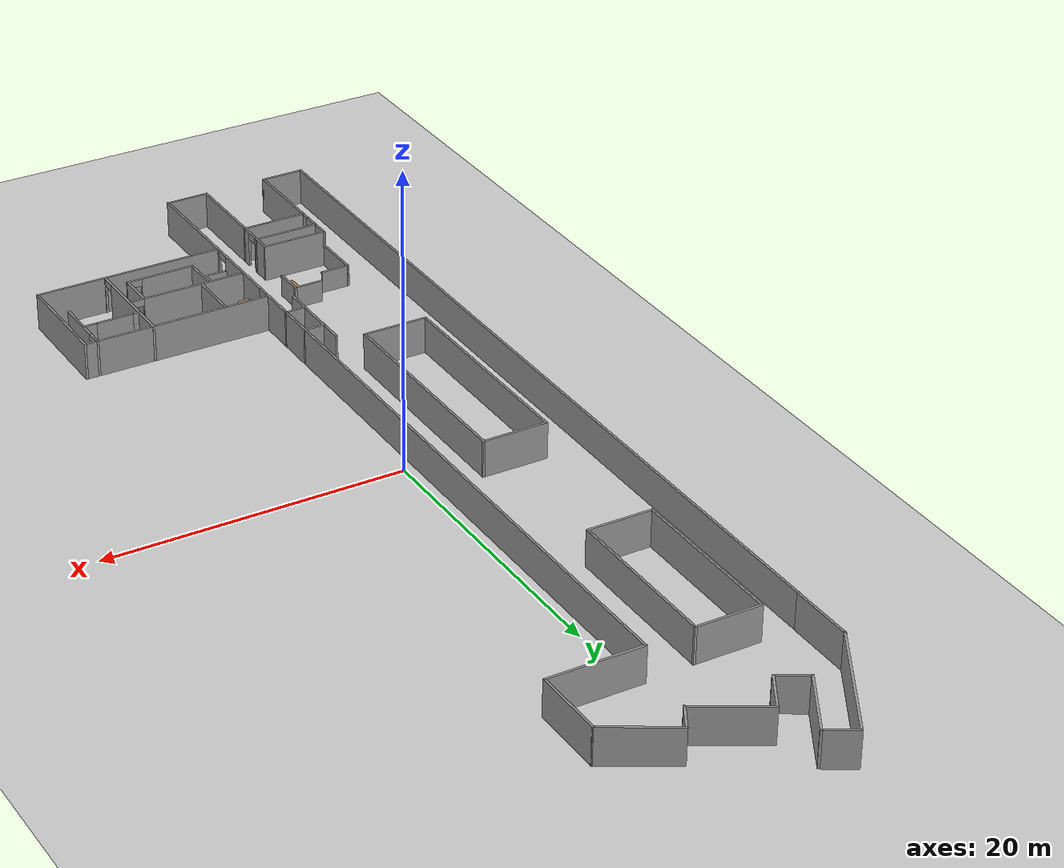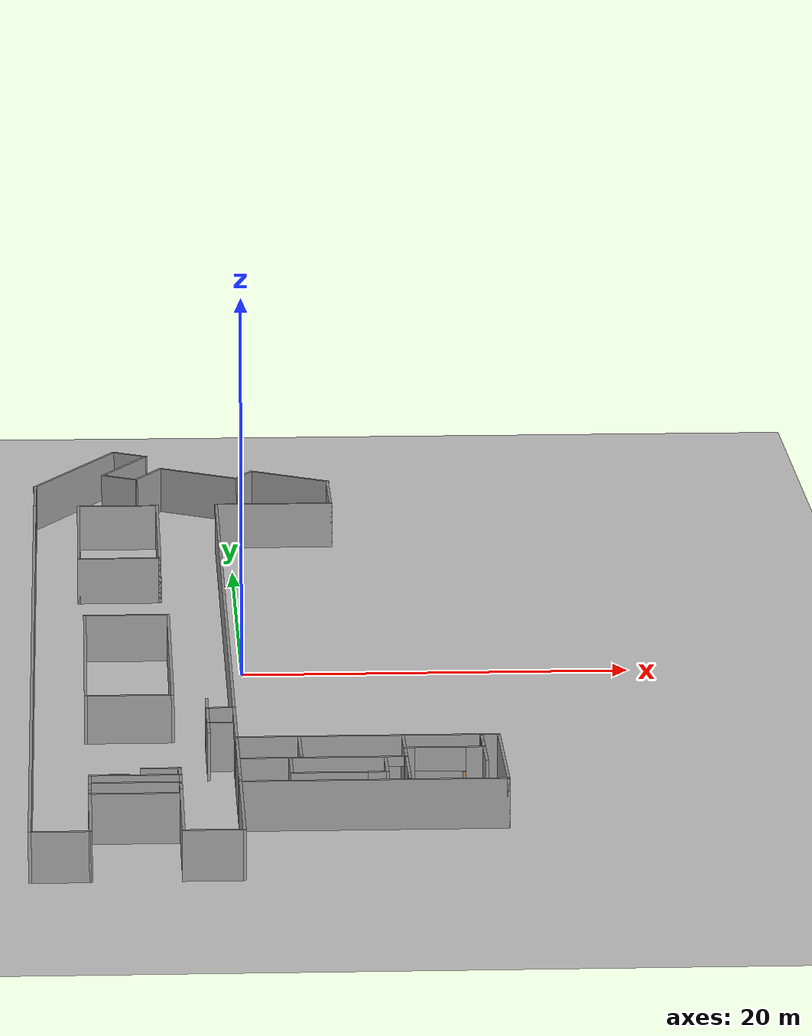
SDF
<sdf version="1.6">
 <world name="default">
  <physics type="ode">
   <max_step_size>0.001</max_step_size>
   <real_time_update_rate>1000</real_time_update_rate>
  </physics>
  <include><uri>model://sun</uri></include>
  <include><uri>model://ground_plane</uri></include>
  <include><uri>model://fei_k5__empty</uri><pose>0.621469 1.46181 0 0 -0 0</pose></include>
  <plugin name="auto_sliding_door_1" filename="libauto_sliding_door.so"><door_name>door1</door_name></plugin>
  <plugin name="auto_sliding_door_2" filename="libauto_sliding_door.so"><door_name>door2</door_name></plugin>
  <model name="table">
   <static>1</static>
   <link name="link">
    <collision name="surface">
     <pose>0 0 1 0 -0 0</pose>
     <geometry><box><size>1.5 0.8 0.03</size></box></geometry>
     <surface><friction><ode><mu>0.6</mu><mu2>0.6</mu2></ode></friction></surface>
    </collision>
    <visual name="visual1">
     <pose>0 0 1 0 -0 0</pose>
     <geometry><box><size>1.5 0.8 0.03</size></box></geometry>
     <material>
      <script><uri>file://media/materials/scripts/gazebo.material</uri><name>Gazebo/Wood</name></script>
     </material>
    </visual>
    <collision name="front_left_leg">
     <pose>0.68 0.38 0.5 0 -0 0</pose>
     <geometry><cylinder><radius>0.02</radius><length>1</length></cylinder></geometry>
    </collision>
    <visual name="front_left_leg">
     <pose>0.68 0.38 0.5 0 -0 0</pose>
     <geometry><cylinder><radius>0.02</radius><length>1</length></cylinder></geometry>
     <material>
      <script><uri>file://media/materials/scripts/gazebo.material</uri><name>Gazebo/Grey</name></script>
     </material>
    </visual>
    <collision name="front_right_leg">
     <pose>0.68 -0.38 0.5 0 -0 0</pose>
     <geometry><cylinder><radius>0.02</radius><length>1</length></cylinder></geometry>
    </collision>
    <visual name="front_right_leg">
     <pose>0.68 -0.38 0.5 0 -0 0</pose>
     <geometry><cylinder><radius>0.02</radius><length>1</length></cylinder></geometry>
     <material>
      <script><uri>file://media/materials/scripts/gazebo.material</uri><name>Gazebo/Grey</name></script>
     </material>
    </visual>
    <collision name="back_right_leg">
     <pose>-0.68 -0.38 0.5 0 -0 0</pose>
     <geometry><cylinder><radius>0.02</radius><length>1</length></cylinder></geometry>
    </collision>
    <visual name="back_right_leg">
     <pose>-0.68 -0.38 0.5 0 -0 0</pose>
     <geometry><cylinder><radius>0.02</radius><length>1</length></cylinder></geometry>
     <material>
      <script><uri>file://media/materials/scripts/gazebo.material</uri><name>Gazebo/Grey</name></script>
     </material>
    </visual>
    <collision name="back_left_leg">
     <pose>-0.68 0.38 0.5 0 -0 0</pose>
     <geometry><cylinder><radius>0.02</radius><length>1</length></cylinder></geometry>
    </collision>
    <visual name="back_left_leg">
     <pose>-0.68 0.38 0.5 0 -0 0</pose>
     <geometry><cylinder><radius>0.02</radius><length>1</length></cylinder></geometry>
     <material>
      <script><uri>file://media/materials/scripts/gazebo.material</uri><name>Gazebo/Grey</name></script>
     </material>
    </visual>
   </link>
   <pose>-0.260512 -21.4438 0 0 -0 1.5708</pose>
  </model>
  <model name="bookshelf_clone">
   <static>1</static>
   <link name="link">
    <inertial><mass>1</mass></inertial>
    <collision name="back">
     <pose>0 0.005 0.6 0 -0 0</pose>
     <geometry><box><size>0.9 0.01 1.2</size></box></geometry>
    </collision>
    <visual name="visual1">
     <pose>0 0.005 0.6 0 -0 0</pose>
     <geometry><box><size>0.9 0.01 1.2</size></box></geometry>
     <material>
      <script><uri>file://media/materials/scripts/gazebo.material</uri><name>Gazebo/Wood</name></script>
     </material>
    </visual>
    <collision name="left_side">
     <pose>0.45 -0.195 0.6 0 -0 0</pose>
     <geometry><box><size>0.02 0.4 1.2</size></box></geometry>
    </collision>
    <visual name="visual2">
     <pose>0.45 -0.195 0.6 0 -0 0</pose>
     <geometry><box><size>0.02 0.4 1.2</size></box></geometry>
     <material>
      <script><uri>file://media/materials/scripts/gazebo.material</uri><name>Gazebo/Wood</name></script>
     </material>
    </visual>
    <collision name="right_side">
     <pose>-0.45 -0.195 0.6 0 -0 0</pose>
     <geometry><box><size>0.02 0.4 1.2</size></box></geometry>
    </collision>
    <visual name="visual3">
     <pose>-0.45 -0.195 0.6 0 -0 0</pose>
     <geometry><box><size>0.02 0.4 1.2</size></box></geometry>
     <material>
      <script><uri>file://media/materials/scripts/gazebo.material</uri><name>Gazebo/Wood</name></script>
     </material>
    </visual>
    <collision name="bottom">
     <pose>0 -0.195 0.03 0 -0 0</pose>
     <geometry><box><size>0.88 0.4 0.06</size></box></geometry>
    </collision>
    <visual name="visual4">
     <pose>0 -0.195 0.03 0 -0 0</pose>
     <geometry><box><size>0.88 0.4 0.06</size></box></geometry>
     <material>
      <script><uri>file://media/materials/scripts/gazebo.material</uri><name>Gazebo/Wood</name></script>
     </material>
    </visual>
    <collision name="top">
     <pose>0 -0.195 1.19 0 -0 0</pose>
     <geometry><box><size>0.88 0.4 0.02</size></box></geometry>
    </collision>
    <visual name="visual5">
     <pose>0 -0.195 1.19 0 -0 0</pose>
     <geometry><box><size>0.88 0.4 0.02</size></box></geometry>
     <material>
      <script><uri>file://media/materials/scripts/gazebo.material</uri><name>Gazebo/Wood</name></script>
     </material>
    </visual>
    <collision name="low_shelf">
     <pose>0 -0.195 0.43 0 -0 0</pose>
     <geometry><box><size>0.88 0.4 0.02</size></box></geometry>
    </collision>
    <visual name="visual6">
     <pose>0 -0.195 0.43 0 -0 0</pose>
     <geometry><box><size>0.88 0.4 0.02</size></box></geometry>
     <material>
      <script><uri>file://media/materials/scripts/gazebo.material</uri><name>Gazebo/Wood</name></script>
     </material>
    </visual>
    <collision name="high_shelf">
     <pose>0 -0.195 0.8 0 -0 0</pose>
     <geometry><box><size>0.88 0.4 0.02</size></box></geometry>
    </collision>
    <visual name="visual7">
     <pose>0 -0.195 0.8 0 -0 0</pose>
     <geometry><box><size>0.88 0.4 0.02</size></box></geometry>
     <material>
      <script><uri>file://media/materials/scripts/gazebo.material</uri><name>Gazebo/Wood</name></script>
     </material>
    </visual>
   </link>
   <pose>-3.74719 -22.2588 0 0 0 -1.59427</pose>
  </model>
  <model name="bookshelf_0">
   <static>1</static>
   <link name="link">
    <inertial><mass>1</mass></inertial>
    <collision name="back">
     <pose>0 0.005 0.6 0 -0 0</pose>
     <geometry><box><size>0.9 0.01 1.2</size></box></geometry>
    </collision>
    <visual name="visual1">
     <pose>0 0.005 0.6 0 -0 0</pose>
     <geometry><box><size>0.9 0.01 1.2</size></box></geometry>
     <material>
      <script><uri>file://media/materials/scripts/gazebo.material</uri><name>Gazebo/Wood</name></script>
     </material>
    </visual>
    <collision name="left_side">
     <pose>0.45 -0.195 0.6 0 -0 0</pose>
     <geometry><box><size>0.02 0.4 1.2</size></box></geometry>
    </collision>
    <visual name="visual2">
     <pose>0.45 -0.195 0.6 0 -0 0</pose>
     <geometry><box><size>0.02 0.4 1.2</size></box></geometry>
     <material>
      <script><uri>file://media/materials/scripts/gazebo.material</uri><name>Gazebo/Wood</name></script>
     </material>
    </visual>
    <collision name="right_side">
     <pose>-0.45 -0.195 0.6 0 -0 0</pose>
     <geometry><box><size>0.02 0.4 1.2</size></box></geometry>
    </collision>
    <visual name="visual3">
     <pose>-0.45 -0.195 0.6 0 -0 0</pose>
     <geometry><box><size>0.02 0.4 1.2</size></box></geometry>
     <material>
      <script><uri>file://media/materials/scripts/gazebo.material</uri><name>Gazebo/Wood</name></script>
     </material>
    </visual>
    <collision name="bottom">
     <pose>0 -0.195 0.03 0 -0 0</pose>
     <geometry><box><size>0.88 0.4 0.06</size></box></geometry>
    </collision>
    <visual name="visual4">
     <pose>0 -0.195 0.03 0 -0 0</pose>
     <geometry><box><size>0.88 0.4 0.06</size></box></geometry>
     <material>
      <script><uri>file://media/materials/scripts/gazebo.material</uri><name>Gazebo/Wood</name></script>
     </material>
    </visual>
    <collision name="top">
     <pose>0 -0.195 1.19 0 -0 0</pose>
     <geometry><box><size>0.88 0.4 0.02</size></box></geometry>
    </collision>
    <visual name="visual5">
     <pose>0 -0.195 1.19 0 -0 0</pose>
     <geometry><box><size>0.88 0.4 0.02</size></box></geometry>
     <material>
      <script><uri>file://media/materials/scripts/gazebo.material</uri><name>Gazebo/Wood</name></script>
     </material>
    </visual>
    <collision name="low_shelf">
     <pose>0 -0.195 0.43 0 -0 0</pose>
     <geometry><box><size>0.88 0.4 0.02</size></box></geometry>
    </collision>
    <visual name="visual6">
     <pose>0 -0.195 0.43 0 -0 0</pose>
     <geometry><box><size>0.88 0.4 0.02</size></box></geometry>
     <material>
      <script><uri>file://media/materials/scripts/gazebo.material</uri><name>Gazebo/Wood</name></script>
     </material>
    </visual>
    <collision name="high_shelf">
     <pose>0 -0.195 0.8 0 -0 0</pose>
     <geometry><box><size>0.88 0.4 0.02</size></box></geometry>
    </collision>
    <visual name="visual7">
     <pose>0 -0.195 0.8 0 -0 0</pose>
     <geometry><box><size>0.88 0.4 0.02</size></box></geometry>
     <material>
      <script><uri>file://media/materials/scripts/gazebo.material</uri><name>Gazebo/Wood</name></script>
     </material>
    </visual>
   </link>
   <pose>10.6702 -21.4467 0 0 -0 3.10949</pose>
  </model>
  <model name="bookshelf_1">
   <static>1</static>
   <link name="link">
    <inertial><mass>1</mass></inertial>
    <collision name="back">
     <pose>0 0.005 0.6 0 -0 0</pose>
     <geometry><box><size>0.9 0.01 1.2</size></box></geometry>
    </collision>
    <visual name="visual1">
     <pose>0 0.005 0.6 0 -0 0</pose>
     <geometry><box><size>0.9 0.01 1.2</size></box></geometry>
     <material>
      <script><uri>file://media/materials/scripts/gazebo.material</uri><name>Gazebo/Wood</name></script>
     </material>
    </visual>
    <collision name="left_side">
     <pose>0.45 -0.195 0.6 0 -0 0</pose>
     <geometry><box><size>0.02 0.4 1.2</size></box></geometry>
    </collision>
    <visual name="visual2">
     <pose>0.45 -0.195 0.6 0 -0 0</pose>
     <geometry><box><size>0.02 0.4 1.2</size></box></geometry>
     <material>
      <script><uri>file://media/materials/scripts/gazebo.material</uri><name>Gazebo/Wood</name></script>
     </material>
    </visual>
    <collision name="right_side">
     <pose>-0.45 -0.195 0.6 0 -0 0</pose>
     <geometry><box><size>0.02 0.4 1.2</size></box></geometry>
    </collision>
    <visual name="visual3">
     <pose>-0.45 -0.195 0.6 0 -0 0</pose>
     <geometry><box><size>0.02 0.4 1.2</size></box></geometry>
     <material>
      <script><uri>file://media/materials/scripts/gazebo.material</uri><name>Gazebo/Wood</name></script>
     </material>
    </visual>
    <collision name="bottom">
     <pose>0 -0.195 0.03 0 -0 0</pose>
     <geometry><box><size>0.88 0.4 0.06</size></box></geometry>
    </collision>
    <visual name="visual4">
     <pose>0 -0.195 0.03 0 -0 0</pose>
     <geometry><box><size>0.88 0.4 0.06</size></box></geometry>
     <material>
      <script><uri>file://media/materials/scripts/gazebo.material</uri><name>Gazebo/Wood</name></script>
     </material>
    </visual>
    <collision name="top">
     <pose>0 -0.195 1.19 0 -0 0</pose>
     <geometry><box><size>0.88 0.4 0.02</size></box></geometry>
    </collision>
    <visual name="visual5">
     <pose>0 -0.195 1.19 0 -0 0</pose>
     <geometry><box><size>0.88 0.4 0.02</size></box></geometry>
     <material>
      <script><uri>file://media/materials/scripts/gazebo.material</uri><name>Gazebo/Wood</name></script>
     </material>
    </visual>
    <collision name="low_shelf">
     <pose>0 -0.195 0.43 0 -0 0</pose>
     <geometry><box><size>0.88 0.4 0.02</size></box></geometry>
    </collision>
    <visual name="visual6">
     <pose>0 -0.195 0.43 0 -0 0</pose>
     <geometry><box><size>0.88 0.4 0.02</size></box></geometry>
     <material>
      <script><uri>file://media/materials/scripts/gazebo.material</uri><name>Gazebo/Wood</name></script>
     </material>
    </visual>
    <collision name="high_shelf">
     <pose>0 -0.195 0.8 0 -0 0</pose>
     <geometry><box><size>0.88 0.4 0.02</size></box></geometry>
    </collision>
    <visual name="visual7">
     <pose>0 -0.195 0.8 0 -0 0</pose>
     <geometry><box><size>0.88 0.4 0.02</size></box></geometry>
     <material>
      <script><uri>file://media/materials/scripts/gazebo.material</uri><name>Gazebo/Wood</name></script>
     </material>
    </visual>
   </link>
   <pose>7.53357 -19.9776 0 0 -0 1.54853</pose>
  </model>
  <model name="bookshelf_2">
   <static>1</static>
   <link name="link">
    <inertial><mass>1</mass></inertial>
    <collision name="back">
     <pose>0 0.005 0.6 0 -0 0</pose>
     <geometry><box><size>0.9 0.01 1.2</size></box></geometry>
    </collision>
    <visual name="visual1">
     <pose>0 0.005 0.6 0 -0 0</pose>
     <geometry><box><size>0.9 0.01 1.2</size></box></geometry>
     <material>
      <script><uri>file://media/materials/scripts/gazebo.material</uri><name>Gazebo/Wood</name></script>
     </material>
    </visual>
    <collision name="left_side">
     <pose>0.45 -0.195 0.6 0 -0 0</pose>
     <geometry><box><size>0.02 0.4 1.2</size></box></geometry>
    </collision>
    <visual name="visual2">
     <pose>0.45 -0.195 0.6 0 -0 0</pose>
     <geometry><box><size>0.02 0.4 1.2</size></box></geometry>
     <material>
      <script><uri>file://media/materials/scripts/gazebo.material</uri><name>Gazebo/Wood</name></script>
     </material>
    </visual>
    <collision name="right_side">
     <pose>-0.45 -0.195 0.6 0 -0 0</pose>
     <geometry><box><size>0.02 0.4 1.2</size></box></geometry>
    </collision>
    <visual name="visual3">
     <pose>-0.45 -0.195 0.6 0 -0 0</pose>
     <geometry><box><size>0.02 0.4 1.2</size></box></geometry>
     <material>
      <script><uri>file://media/materials/scripts/gazebo.material</uri><name>Gazebo/Wood</name></script>
     </material>
    </visual>
    <collision name="bottom">
     <pose>0 -0.195 0.03 0 -0 0</pose>
     <geometry><box><size>0.88 0.4 0.06</size></box></geometry>
    </collision>
    <visual name="visual4">
     <pose>0 -0.195 0.03 0 -0 0</pose>
     <geometry><box><size>0.88 0.4 0.06</size></box></geometry>
     <material>
      <script><uri>file://media/materials/scripts/gazebo.material</uri><name>Gazebo/Wood</name></script>
     </material>
    </visual>
    <collision name="top">
     <pose>0 -0.195 1.19 0 -0 0</pose>
     <geometry><box><size>0.88 0.4 0.02</size></box></geometry>
    </collision>
    <visual name="visual5">
     <pose>0 -0.195 1.19 0 -0 0</pose>
     <geometry><box><size>0.88 0.4 0.02</size></box></geometry>
     <material>
      <script><uri>file://media/materials/scripts/gazebo.material</uri><name>Gazebo/Wood</name></script>
     </material>
    </visual>
    <collision name="low_shelf">
     <pose>0 -0.195 0.43 0 -0 0</pose>
     <geometry><box><size>0.88 0.4 0.02</size></box></geometry>
    </collision>
    <visual name="visual6">
     <pose>0 -0.195 0.43 0 -0 0</pose>
     <geometry><box><size>0.88 0.4 0.02</size></box></geometry>
     <material>
      <script><uri>file://media/materials/scripts/gazebo.material</uri><name>Gazebo/Wood</name></script>
     </material>
    </visual>
    <collision name="high_shelf">
     <pose>0 -0.195 0.8 0 -0 0</pose>
     <geometry><box><size>0.88 0.4 0.02</size></box></geometry>
    </collision>
    <visual name="visual7">
     <pose>0 -0.195 0.8 0 -0 0</pose>
     <geometry><box><size>0.88 0.4 0.02</size></box></geometry>
     <material>
      <script><uri>file://media/materials/scripts/gazebo.material</uri><name>Gazebo/Wood</name></script>
     </material>
    </visual>
   </link>
   <pose>1.85213 -24.7211 0 0 -0 1.58503</pose>
  </model>
  <model name="bookshelf_3">
   <static>1</static>
   <link name="link">
    <inertial><mass>1</mass></inertial>
    <collision name="back">
     <pose>0 0.005 0.6 0 -0 0</pose>
     <geometry><box><size>0.9 0.01 1.2</size></box></geometry>
    </collision>
    <visual name="visual1">
     <pose>0 0.005 0.6 0 -0 0</pose>
     <geometry><box><size>0.9 0.01 1.2</size></box></geometry>
     <material>
      <script><uri>file://media/materials/scripts/gazebo.material</uri><name>Gazebo/Wood</name></script>
     </material>
    </visual>
    <collision name="left_side">
     <pose>0.45 -0.195 0.6 0 -0 0</pose>
     <geometry><box><size>0.02 0.4 1.2</size></box></geometry>
    </collision>
    <visual name="visual2">
     <pose>0.45 -0.195 0.6 0 -0 0</pose>
     <geometry><box><size>0.02 0.4 1.2</size></box></geometry>
     <material>
      <script><uri>file://media/materials/scripts/gazebo.material</uri><name>Gazebo/Wood</name></script>
     </material>
    </visual>
    <collision name="right_side">
     <pose>-0.45 -0.195 0.6 0 -0 0</pose>
     <geometry><box><size>0.02 0.4 1.2</size></box></geometry>
    </collision>
    <visual name="visual3">
     <pose>-0.45 -0.195 0.6 0 -0 0</pose>
     <geometry><box><size>0.02 0.4 1.2</size></box></geometry>
     <material>
      <script><uri>file://media/materials/scripts/gazebo.material</uri><name>Gazebo/Wood</name></script>
     </material>
    </visual>
    <collision name="bottom">
     <pose>0 -0.195 0.03 0 -0 0</pose>
     <geometry><box><size>0.88 0.4 0.06</size></box></geometry>
    </collision>
    <visual name="visual4">
     <pose>0 -0.195 0.03 0 -0 0</pose>
     <geometry><box><size>0.88 0.4 0.06</size></box></geometry>
     <material>
      <script><uri>file://media/materials/scripts/gazebo.material</uri><name>Gazebo/Wood</name></script>
     </material>
    </visual>
    <collision name="top">
     <pose>0 -0.195 1.19 0 -0 0</pose>
     <geometry><box><size>0.88 0.4 0.02</size></box></geometry>
    </collision>
    <visual name="visual5">
     <pose>0 -0.195 1.19 0 -0 0</pose>
     <geometry><box><size>0.88 0.4 0.02</size></box></geometry>
     <material>
      <script><uri>file://media/materials/scripts/gazebo.material</uri><name>Gazebo/Wood</name></script>
     </material>
    </visual>
    <collision name="low_shelf">
     <pose>0 -0.195 0.43 0 -0 0</pose>
     <geometry><box><size>0.88 0.4 0.02</size></box></geometry>
    </collision>
    <visual name="visual6">
     <pose>0 -0.195 0.43 0 -0 0</pose>
     <geometry><box><size>0.88 0.4 0.02</size></box></geometry>
     <material>
      <script><uri>file://media/materials/scripts/gazebo.material</uri><name>Gazebo/Wood</name></script>
     </material>
    </visual>
    <collision name="high_shelf">
     <pose>0 -0.195 0.8 0 -0 0</pose>
     <geometry><box><size>0.88 0.4 0.02</size></box></geometry>
    </collision>
    <visual name="visual7">
     <pose>0 -0.195 0.8 0 -0 0</pose>
     <geometry><box><size>0.88 0.4 0.02</size></box></geometry>
     <material>
      <script><uri>file://media/materials/scripts/gazebo.material</uri><name>Gazebo/Wood</name></script>
     </material>
    </visual>
   </link>
   <pose>1.85241 -23.7046 0 0 -0 1.56923</pose>
  </model>
 </world>
</sdf>

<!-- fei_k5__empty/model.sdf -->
<sdf version='1.6'>

  <model name='fei_k5__empty'>
    <pose>0 0 0 0 0 0</pose>

    <link name='Wall_10'>
      <collision name='Wall_10_Collision'>
        <geometry>
          <box>
            <size>4.5 0.15 2.5</size>
          </box>
        </geometry>
        <pose>0 0 1.25 0 -0 0</pose>
        <max_contacts>10</max_contacts>
        <surface>
          <contact>
            <ode/>
          </contact>
          <bounce/>
          <friction>
            <torsional>
              <ode/>
            </torsional>
            <ode/>
          </friction>
        </surface>
      </collision>
      <visual name='Wall_10_Visual'>
        <pose>0 0 1.25 0 -0 0</pose>
        <geometry>
          <box>
            <size>4.5 0.15 2.5</size>
          </box>
        </geometry>
        <material>
          <script>
            <uri>file://media/materials/scripts/gazebo.material</uri>
            <name>Gazebo/Grey</name>
          </script>
          <ambient>1 1 1 1</ambient>
        </material>
        <meta>
          <layer>0</layer>
        </meta>
      </visual>
      <pose>-6.57828 1.39977 0 0 -0 3.14159</pose>
      <self_collide>0</self_collide>
      <enable_wind>0</enable_wind>
      <kinematic>0</kinematic>
    </link>
    <link name='Wall_11'>
      <collision name='Wall_11_Collision'>
        <geometry>
          <box>
            <size>15 0.15 2.5</size>
          </box>
        </geometry>
        <pose>0 0 1.25 0 -0 0</pose>
        <max_contacts>10</max_contacts>
        <surface>
          <contact>
            <ode/>
          </contact>
          <bounce/>
          <friction>
            <torsional>
              <ode/>
            </torsional>
            <ode/>
          </friction>
        </surface>
      </collision>
      <visual name='Wall_11_Visual'>
        <pose>0 0 1.25 0 -0 0</pose>
        <geometry>
          <box>
            <size>15 0.15 2.5</size>
          </box>
        </geometry>
        <material>
          <script>
            <uri>file://media/materials/scripts/gazebo.material</uri>
            <name>Gazebo/Grey</name>
          </script>
          <ambient>1 1 1 1</ambient>
        </material>
        <meta>
          <layer>0</layer>
        </meta>
      </visual>
      <pose>-8.75328 -6.02523 0 0 -0 -1.5708</pose>
      <self_collide>0</self_collide>
      <enable_wind>0</enable_wind>
      <kinematic>0</kinematic>
    </link>
    <link name='Wall_16'>
      <collision name='Wall_16_Collision'>
        <geometry>
          <box>
            <size>4.5 0.15 2.5</size>
          </box>
        </geometry>
        <pose>0 0 1.25 0 -0 0</pose>
        <max_contacts>10</max_contacts>
        <surface>
          <contact>
            <ode/>
          </contact>
          <bounce/>
          <friction>
            <torsional>
              <ode/>
            </torsional>
            <ode/>
          </friction>
        </surface>
      </collision>
      <visual name='Wall_16_Visual'>
        <pose>0 0 1.25 0 -0 0</pose>
        <geometry>
          <box>
            <size>4.5 0.15 2.5</size>
          </box>
        </geometry>
        <material>
          <script>
            <uri>file://media/materials/scripts/gazebo.material</uri>
            <name>Gazebo/Grey</name>
          </script>
          <ambient>1 1 1 1</ambient>
        </material>
        <meta>
          <layer>0</layer>
        </meta>
      </visual>
      <pose>-6.85668 12.6908 0 0 -0 0</pose>
      <self_collide>0</self_collide>
      <enable_wind>0</enable_wind>
      <kinematic>0</kinematic>
    </link>
    <link name='Wall_17'>
      <collision name='Wall_17_Collision'>
        <geometry>
          <box>
            <size>11.25 0.15 2.5</size>
          </box>
        </geometry>
        <pose>0 0 1.25 0 -0 0</pose>
        <max_contacts>10</max_contacts>
        <surface>
          <contact>
            <ode/>
          </contact>
          <bounce/>
          <friction>
            <torsional>
              <ode/>
            </torsional>
            <ode/>
          </friction>
        </surface>
      </collision>
      <visual name='Wall_17_Visual'>
        <pose>0 0 1.25 0 -0 0</pose>
        <geometry>
          <box>
            <size>11.25 0.15 2.5</size>
          </box>
        </geometry>
        <material>
          <script>
            <uri>file://media/materials/scripts/gazebo.material</uri>
            <name>Gazebo/Grey</name>
          </script>
          <ambient>1 1 1 1</ambient>
        </material>
        <meta>
          <layer>0</layer>
        </meta>
      </visual>
      <pose>-4.68168 18.2408 0 0 -0 1.5708</pose>
      <self_collide>0</self_collide>
      <enable_wind>0</enable_wind>
      <kinematic>0</kinematic>
    </link>
    <link name='Wall_18'>
      <collision name='Wall_18_Collision'>
        <geometry>
          <box>
            <size>4.5 0.15 2.5</size>
          </box>
        </geometry>
        <pose>0 0 1.25 0 -0 0</pose>
        <max_contacts>10</max_contacts>
        <surface>
          <contact>
            <ode/>
          </contact>
          <bounce/>
          <friction>
            <torsional>
              <ode/>
            </torsional>
            <ode/>
          </friction>
        </surface>
      </collision>
      <visual name='Wall_18_Visual'>
        <pose>0 0 1.25 0 -0 0</pose>
        <geometry>
          <box>
            <size>4.5 0.15 2.5</size>
          </box>
        </geometry>
        <material>
          <script>
            <uri>file://media/materials/scripts/gazebo.material</uri>
            <name>Gazebo/Grey</name>
          </script>
          <ambient>1 1 1 1</ambient>
        </material>
        <meta>
          <layer>0</layer>
        </meta>
      </visual>
      <pose>-6.85668 23.7908 0 0 -0 3.14159</pose>
      <self_collide>0</self_collide>
      <enable_wind>0</enable_wind>
      <kinematic>0</kinematic>
    </link>
    <link name='Wall_19'>
      <collision name='Wall_19_Collision'>
        <geometry>
          <box>
            <size>11.25 0.15 2.5</size>
          </box>
        </geometry>
        <pose>0 0 1.25 0 -0 0</pose>
        <max_contacts>10</max_contacts>
        <surface>
          <contact>
            <ode/>
          </contact>
          <bounce/>
          <friction>
            <torsional>
              <ode/>
            </torsional>
            <ode/>
          </friction>
        </surface>
      </collision>
      <visual name='Wall_19_Visual'>
        <pose>0 0 1.25 0 -0 0</pose>
        <geometry>
          <box>
            <size>11.25 0.15 2.5</size>
          </box>
        </geometry>
        <material>
          <script>
            <uri>file://media/materials/scripts/gazebo.material</uri>
            <name>Gazebo/Grey</name>
          </script>
          <ambient>1 1 1 1</ambient>
        </material>
        <meta>
          <layer>0</layer>
        </meta>
      </visual>
      <pose>-9.03168 18.2408 0 0 -0 -1.5708</pose>
      <self_collide>0</self_collide>
      <enable_wind>0</enable_wind>
      <kinematic>0</kinematic>
    </link>
    <link name='Wall_21'>
      <collision name='Wall_21_Collision'>
        <geometry>
          <box>
            <size>3 0.15 2.5</size>
          </box>
        </geometry>
        <pose>0 0 1.25 0 -0 0</pose>
        <max_contacts>10</max_contacts>
        <surface>
          <contact>
            <ode/>
          </contact>
          <bounce/>
          <friction>
            <torsional>
              <ode/>
            </torsional>
            <ode/>
          </friction>
        </surface>
      </collision>
      <visual name='Wall_21_Visual'>
        <pose>0 0 1.25 0 -0 0</pose>
        <geometry>
          <box>
            <size>3 0.15 2.5</size>
          </box>
        </geometry>
        <material>
          <script>
            <uri>file://media/materials/scripts/gazebo.material</uri>
            <name>Gazebo/Grey</name>
          </script>
          <ambient>1 1 1 1</ambient>
        </material>
        <meta>
          <layer>0</layer>
        </meta>
      </visual>
      <pose>-2.81965 -35.9036 0 0 -0 0</pose>
      <self_collide>0</self_collide>
      <enable_wind>0</enable_wind>
      <kinematic>0</kinematic>
    </link>
    <link name='Wall_22'>
      <pose>-1.39465 -5.97863 0 0 -0 1.5708</pose>
      <visual name='Wall_22_Visual_0'>
        <pose>-25.9925 0 1.25 0 -0 0</pose>
        <geometry>
          <box>
            <size>8.01507 0.15 2.5</size>
          </box>
        </geometry>
        <material>
          <script>
            <uri>file://media/materials/scripts/gazebo.material</uri>
            <name>Gazebo/Grey</name>
          </script>
          <ambient>1 1 1 1</ambient>
        </material>
        <meta>
          <layer>0</layer>
        </meta>
      </visual>
      <collision name='Wall_22_Collision_0'>
        <geometry>
          <box>
            <size>8.01507 0.15 2.5</size>
          </box>
        </geometry>
        <pose>-25.9925 0 1.25 0 -0 0</pose>
        <max_contacts>10</max_contacts>
        <surface>
          <contact>
            <ode/>
          </contact>
          <bounce/>
          <friction>
            <torsional>
              <ode/>
            </torsional>
            <ode/>
          </friction>
        </surface>
      </collision>
      <visual name='Wall_22_Visual_1'>
        <pose>-18.5953 0 1.25 0 -0 0</pose>
        <geometry>
          <box>
            <size>4.97924 0.15 2.5</size>
          </box>
        </geometry>
        <material>
          <script>
            <uri>file://media/materials/scripts/gazebo.material</uri>
            <name>Gazebo/Grey</name>
          </script>
          <ambient>1 1 1 1</ambient>
        </material>
        <meta>
          <layer>0</layer>
        </meta>
      </visual>
      <collision name='Wall_22_Collision_1'>
        <geometry>
          <box>
            <size>4.97924 0.15 2.5</size>
          </box>
        </geometry>
        <pose>-18.5953 0 1.25 0 -0 0</pose>
        <max_contacts>10</max_contacts>
        <surface>
          <contact>
            <ode/>
          </contact>
          <bounce/>
          <friction>
            <torsional>
              <ode/>
            </torsional>
            <ode/>
          </friction>
        </surface>
      </collision>
      <visual name='Wall_22_Visual_2'>
        <pose>7.39715 0 1.25 0 -0 0</pose>
        <geometry>
          <box>
            <size>45.2057 0.15 2.5</size>
          </box>
        </geometry>
        <material>
          <script>
            <uri>file://media/materials/scripts/gazebo.material</uri>
            <name>Gazebo/Grey</name>
          </script>
          <ambient>1 1 1 1</ambient>
        </material>
        <meta>
          <layer>0</layer>
        </meta>
      </visual>
      <collision name='Wall_22_Collision_2'>
        <geometry>
          <box>
            <size>45.2057 0.15 2.5</size>
          </box>
        </geometry>
        <pose>7.39715 0 1.25 0 -0 0</pose>
        <max_contacts>10</max_contacts>
        <surface>
          <contact>
            <ode/>
          </contact>
          <bounce/>
          <friction>
            <torsional>
              <ode/>
            </torsional>
            <ode/>
          </friction>
        </surface>
      </collision>
      <visual name='Wall_22_Visual_3'>
        <pose>-21.5349 0 2.25 0 -0 0</pose>
        <geometry>
          <box>
            <size>0.9 0.15 0.5</size>
          </box>
        </geometry>
        <material>
          <script>
            <uri>file://media/materials/scripts/gazebo.material</uri>
            <name>Gazebo/Grey</name>
          </script>
          <ambient>1 1 1 1</ambient>
        </material>
        <meta>
          <layer>0</layer>
        </meta>
      </visual>
      <collision name='Wall_22_Collision_3'>
        <geometry>
          <box>
            <size>0.9 0.15 0.5</size>
          </box>
        </geometry>
        <pose>-21.5349 0 2.25 0 -0 0</pose>
        <max_contacts>10</max_contacts>
        <surface>
          <contact>
            <ode/>
          </contact>
          <bounce/>
          <friction>
            <torsional>
              <ode/>
            </torsional>
            <ode/>
          </friction>
        </surface>
      </collision>
      <visual name='Wall_22_Visual_4'>
        <pose>-15.6557 0 2.25 0 -0 0</pose>
        <geometry>
          <box>
            <size>0.9 0.15 0.5</size>
          </box>
        </geometry>
        <material>
          <script>
            <uri>file://media/materials/scripts/gazebo.material</uri>
            <name>Gazebo/Grey</name>
          </script>
          <ambient>1 1 1 1</ambient>
        </material>
        <meta>
          <layer>0</layer>
        </meta>
      </visual>
      <collision name='Wall_22_Collision_4'>
        <geometry>
          <box>
            <size>0.9 0.15 0.5</size>
          </box>
        </geometry>
        <pose>-15.6557 0 2.25 0 -0 0</pose>
        <max_contacts>10</max_contacts>
        <surface>
          <contact>
            <ode/>
          </contact>
          <bounce/>
          <friction>
            <torsional>
              <ode/>
            </torsional>
            <ode/>
          </friction>
        </surface>
      </collision>
      <self_collide>0</self_collide>
      <enable_wind>0</enable_wind>
      <kinematic>0</kinematic>
    </link>
    <link name='Wall_24'>
      <collision name='Wall_24_Collision'>
        <geometry>
          <box>
            <size>6.5 0.15 2.5</size>
          </box>
        </geometry>
        <pose>0 0 1.25 0 -0 0</pose>
        <max_contacts>10</max_contacts>
        <surface>
          <contact>
            <ode/>
          </contact>
          <bounce/>
          <friction>
            <torsional>
              <ode/>
            </torsional>
            <ode/>
          </friction>
        </surface>
      </collision>
      <visual name='Wall_24_Visual'>
        <pose>0 0 1.25 0 -0 0</pose>
        <geometry>
          <box>
            <size>6.5 0.15 2.5</size>
          </box>
        </geometry>
        <material>
          <script>
            <uri>file://media/materials/scripts/gazebo.material</uri>
            <name>Gazebo/Grey</name>
          </script>
          <ambient>1 1 1 1</ambient>
        </material>
        <meta>
          <layer>0</layer>
        </meta>
      </visual>
      <pose>1.78035 23.9464 0 0 -0 0</pose>
      <self_collide>0</self_collide>
      <enable_wind>0</enable_wind>
      <kinematic>0</kinematic>
    </link>
    <link name='Wall_25'>
      <collision name='Wall_25_Collision'>
        <geometry>
          <box>
            <size>5 0.15 2.5</size>
          </box>
        </geometry>
        <pose>0 0 1.25 0 -0 0</pose>
        <max_contacts>10</max_contacts>
        <surface>
          <contact>
            <ode/>
          </contact>
          <bounce/>
          <friction>
            <torsional>
              <ode/>
            </torsional>
            <ode/>
          </friction>
        </surface>
      </collision>
      <visual name='Wall_25_Visual'>
        <pose>0 0 1.25 0 -0 0</pose>
        <geometry>
          <box>
            <size>5 0.15 2.5</size>
          </box>
        </geometry>
        <material>
          <script>
            <uri>file://media/materials/scripts/gazebo.material</uri>
            <name>Gazebo/Grey</name>
          </script>
          <ambient>1 1 1 1</ambient>
        </material>
        <meta>
          <layer>0</layer>
        </meta>
      </visual>
      <pose>4.95535 26.3714 0 0 -0 1.5708</pose>
      <self_collide>0</self_collide>
      <enable_wind>0</enable_wind>
      <kinematic>0</kinematic>
    </link>
    <link name='Wall_26'>
      <collision name='Wall_26_Collision'>
        <geometry>
          <box>
            <size>5 0.15 2.5</size>
          </box>
        </geometry>
        <pose>0 0 1.25 0 -0 0</pose>
        <max_contacts>10</max_contacts>
        <surface>
          <contact>
            <ode/>
          </contact>
          <bounce/>
          <friction>
            <torsional>
              <ode/>
            </torsional>
            <ode/>
          </friction>
        </surface>
      </collision>
      <visual name='Wall_26_Visual'>
        <pose>0 0 1.25 0 -0 0</pose>
        <geometry>
          <box>
            <size>5 0.15 2.5</size>
          </box>
        </geometry>
        <material>
          <script>
            <uri>file://media/materials/scripts/gazebo.material</uri>
            <name>Gazebo/Grey</name>
          </script>
          <ambient>1 1 1 1</ambient>
        </material>
        <meta>
          <layer>0</layer>
        </meta>
      </visual>
      <pose>2.85524 30.0089 0 0 -0 2.61799</pose>
      <self_collide>0</self_collide>
      <enable_wind>0</enable_wind>
      <kinematic>0</kinematic>
    </link>
    <link name='Wall_27'>
      <collision name='Wall_27_Collision'>
        <geometry>
          <box>
            <size>2 0.15 2.5</size>
          </box>
        </geometry>
        <pose>0 0 1.25 0 -0 0</pose>
        <max_contacts>10</max_contacts>
        <surface>
          <contact>
            <ode/>
          </contact>
          <bounce/>
          <friction>
            <torsional>
              <ode/>
            </torsional>
            <ode/>
          </friction>
        </surface>
      </collision>
      <visual name='Wall_27_Visual'>
        <pose>0 0 1.25 0 -0 0</pose>
        <geometry>
          <box>
            <size>2 0.15 2.5</size>
          </box>
        </geometry>
        <material>
          <script>
            <uri>file://media/materials/scripts/gazebo.material</uri>
            <name>Gazebo/Grey</name>
          </script>
          <ambient>1 1 1 1</ambient>
        </material>
        <meta>
          <layer>0</layer>
        </meta>
      </visual>
      <pose>0.292625 30.4203 0 0 -0 -2.0944</pose>
      <self_collide>0</self_collide>
      <enable_wind>0</enable_wind>
      <kinematic>0</kinematic>
    </link>
    <link name='Wall_28'>
      <collision name='Wall_28_Collision'>
        <geometry>
          <box>
            <size>5 0.15 2.5</size>
          </box>
        </geometry>
        <pose>0 0 1.25 0 -0 0</pose>
        <max_contacts>10</max_contacts>
        <surface>
          <contact>
            <ode/>
          </contact>
          <bounce/>
          <friction>
            <torsional>
              <ode/>
            </torsional>
            <ode/>
          </friction>
        </surface>
      </collision>
      <visual name='Wall_28_Visual'>
        <pose>0 0 1.25 0 -0 0</pose>
        <geometry>
          <box>
            <size>5 0.15 2.5</size>
          </box>
        </geometry>
        <material>
          <script>
            <uri>file://media/materials/scripts/gazebo.material</uri>
            <name>Gazebo/Grey</name>
          </script>
          <ambient>1 1 1 1</ambient>
        </material>
        <meta>
          <layer>0</layer>
        </meta>
      </visual>
      <pose>-2.26999 30.8317 0 0 -0 2.61799</pose>
      <self_collide>0</self_collide>
      <enable_wind>0</enable_wind>
      <kinematic>0</kinematic>
    </link>
    <link name='Wall_29'>
      <collision name='Wall_29_Collision'>
        <geometry>
          <box>
            <size>3 0.15 2.5</size>
          </box>
        </geometry>
        <pose>0 0 1.25 0 -0 0</pose>
        <max_contacts>10</max_contacts>
        <surface>
          <contact>
            <ode/>
          </contact>
          <bounce/>
          <friction>
            <torsional>
              <ode/>
            </torsional>
            <ode/>
          </friction>
        </surface>
      </collision>
      <visual name='Wall_29_Visual'>
        <pose>0 0 1.25 0 -0 0</pose>
        <geometry>
          <box>
            <size>3 0.15 2.5</size>
          </box>
        </geometry>
        <material>
          <script>
            <uri>file://media/materials/scripts/gazebo.material</uri>
            <name>Gazebo/Grey</name>
          </script>
          <ambient>1 1 1 1</ambient>
        </material>
        <meta>
          <layer>0</layer>
        </meta>
      </visual>
      <pose>-5.0826 30.8101 0 0 -0 -2.0944</pose>
      <self_collide>0</self_collide>
      <enable_wind>0</enable_wind>
      <kinematic>0</kinematic>
    </link>
    <link name='Wall_30'>
      <collision name='Wall_30_Collision'>
        <geometry>
          <box>
            <size>2.25 0.15 2.5</size>
          </box>
        </geometry>
        <pose>0 0 1.25 0 -0 0</pose>
        <max_contacts>10</max_contacts>
        <surface>
          <contact>
            <ode/>
          </contact>
          <bounce/>
          <friction>
            <torsional>
              <ode/>
            </torsional>
            <ode/>
          </friction>
        </surface>
      </collision>
      <visual name='Wall_30_Visual'>
        <pose>0 0 1.25 0 -0 0</pose>
        <geometry>
          <box>
            <size>2.25 0.15 2.5</size>
          </box>
        </geometry>
        <material>
          <script>
            <uri>file://media/materials/scripts/gazebo.material</uri>
            <name>Gazebo/Grey</name>
          </script>
          <ambient>1 1 1 1</ambient>
        </material>
        <meta>
          <layer>0</layer>
        </meta>
      </visual>
      <pose>-6.70442 30.101 0 0 -0 2.61799</pose>
      <self_collide>0</self_collide>
      <enable_wind>0</enable_wind>
      <kinematic>0</kinematic>
    </link>
    <link name='Wall_31'>
      <collision name='Wall_31_Collision'>
        <geometry>
          <box>
            <size>5 0.15 2.5</size>
          </box>
        </geometry>
        <pose>0 0 1.25 0 -0 0</pose>
        <max_contacts>10</max_contacts>
        <surface>
          <contact>
            <ode/>
          </contact>
          <bounce/>
          <friction>
            <torsional>
              <ode/>
            </torsional>
            <ode/>
          </friction>
        </surface>
      </collision>
      <visual name='Wall_31_Visual'>
        <pose>0 0 1.25 0 -0 0</pose>
        <geometry>
          <box>
            <size>5 0.15 2.5</size>
          </box>
        </geometry>
        <material>
          <script>
            <uri>file://media/materials/scripts/gazebo.material</uri>
            <name>Gazebo/Grey</name>
          </script>
          <ambient>1 1 1 1</ambient>
        </material>
        <meta>
          <layer>0</layer>
        </meta>
      </visual>
      <pose>-6.40125 32.7262 0 0 -0 1.0472</pose>
      <self_collide>0</self_collide>
      <enable_wind>0</enable_wind>
      <kinematic>0</kinematic>
    </link>
    <link name='Wall_32'>
      <collision name='Wall_32_Collision'>
        <geometry>
          <box>
            <size>2.25 0.15 2.5</size>
          </box>
        </geometry>
        <pose>0 0 1.25 0 -0 0</pose>
        <max_contacts>10</max_contacts>
        <surface>
          <contact>
            <ode/>
          </contact>
          <bounce/>
          <friction>
            <torsional>
              <ode/>
            </torsional>
            <ode/>
          </friction>
        </surface>
      </collision>
      <visual name='Wall_32_Visual'>
        <pose>0 0 1.25 0 -0 0</pose>
        <geometry>
          <box>
            <size>2.25 0.15 2.5</size>
          </box>
        </geometry>
        <material>
          <script>
            <uri>file://media/materials/scripts/gazebo.material</uri>
            <name>Gazebo/Grey</name>
          </script>
          <ambient>1 1 1 1</ambient>
        </material>
        <meta>
          <layer>0</layer>
        </meta>
      </visual>
      <pose>-6.09808 35.3513 0 0 -0 2.61799</pose>
      <self_collide>0</self_collide>
      <enable_wind>0</enable_wind>
      <kinematic>0</kinematic>
    </link>
    <link name='Wall_35'>
      <pose>-4.24465 -31.4786 0 0 -0 1.5708</pose>
      <visual name='Wall_35_Visual_0'>
        <pose>-1.19967 0 1.25 0 -0 0</pose>
        <geometry>
          <box>
            <size>6.60065 0.15 2.5</size>
          </box>
        </geometry>
        <material>
          <script>
            <uri>file://media/materials/scripts/gazebo.material</uri>
            <name>Gazebo/Grey</name>
          </script>
          <ambient>1 1 1 1</ambient>
        </material>
        <meta>
          <layer>0</layer>
        </meta>
      </visual>
      <collision name='Wall_35_Collision_0'>
        <geometry>
          <box>
            <size>6.60065 0.15 2.5</size>
          </box>
        </geometry>
        <pose>-1.19967 0 1.25 0 -0 0</pose>
        <max_contacts>10</max_contacts>
        <surface>
          <contact>
            <ode/>
          </contact>
          <bounce/>
          <friction>
            <torsional>
              <ode/>
            </torsional>
            <ode/>
          </friction>
        </surface>
      </collision>
      <visual name='Wall_35_Visual_1'>
        <pose>3.75033 0 1.25 0 -0 0</pose>
        <geometry>
          <box>
            <size>1.49934 0.15 2.5</size>
          </box>
        </geometry>
        <material>
          <script>
            <uri>file://media/materials/scripts/gazebo.material</uri>
            <name>Gazebo/Grey</name>
          </script>
          <ambient>1 1 1 1</ambient>
        </material>
        <meta>
          <layer>0</layer>
        </meta>
      </visual>
      <collision name='Wall_35_Collision_1'>
        <geometry>
          <box>
            <size>1.49934 0.15 2.5</size>
          </box>
        </geometry>
        <pose>3.75033 0 1.25 0 -0 0</pose>
        <max_contacts>10</max_contacts>
        <surface>
          <contact>
            <ode/>
          </contact>
          <bounce/>
          <friction>
            <torsional>
              <ode/>
            </torsional>
            <ode/>
          </friction>
        </surface>
      </collision>
      <visual name='Wall_35_Visual_2'>
        <pose>2.55065 0 2.25 0 -0 0</pose>
        <geometry>
          <box>
            <size>0.9 0.15 0.5</size>
          </box>
        </geometry>
        <material>
          <script>
            <uri>file://media/materials/scripts/gazebo.material</uri>
            <name>Gazebo/Grey</name>
          </script>
          <ambient>1 1 1 1</ambient>
        </material>
        <meta>
          <layer>0</layer>
        </meta>
      </visual>
      <collision name='Wall_35_Collision_2'>
        <geometry>
          <box>
            <size>0.9 0.15 0.5</size>
          </box>
        </geometry>
        <pose>2.55065 0 2.25 0 -0 0</pose>
        <max_contacts>10</max_contacts>
        <surface>
          <contact>
            <ode/>
          </contact>
          <bounce/>
          <friction>
            <torsional>
              <ode/>
            </torsional>
            <ode/>
          </friction>
        </surface>
      </collision>
      <self_collide>0</self_collide>
      <enable_wind>0</enable_wind>
      <kinematic>0</kinematic>
    </link>
    <link name='Wall_36'>
      <collision name='Wall_36_Collision'>
        <geometry>
          <box>
            <size>4.51247 0.15 2.5</size>
          </box>
        </geometry>
        <pose>0 0 1.25 0 -0 0</pose>
        <max_contacts>10</max_contacts>
        <surface>
          <contact>
            <ode/>
          </contact>
          <bounce/>
          <friction>
            <torsional>
              <ode/>
            </torsional>
            <ode/>
          </friction>
        </surface>
      </collision>
      <visual name='Wall_36_Visual'>
        <pose>0 0 1.25 0 -0 0</pose>
        <geometry>
          <box>
            <size>4.51247 0.15 2.5</size>
          </box>
        </geometry>
        <material>
          <script>
            <uri>file://media/materials/scripts/gazebo.material</uri>
            <name>Gazebo/Grey</name>
          </script>
          <ambient>1 1 1 1</ambient>
        </material>
        <meta>
          <layer>0</layer>
        </meta>
      </visual>
      <pose>-6.4254 -27.0536 0 0 -0 -3.14159</pose>
      <self_collide>0</self_collide>
      <enable_wind>0</enable_wind>
      <kinematic>0</kinematic>
    </link>
    <link name='Wall_37'>
      <pose>-8.6004 -31.4786 0 0 -0 -1.5695</pose>
      <visual name='Wall_37_Visual_0'>
        <pose>-3.75035 0 1.25 0 -0 0</pose>
        <geometry>
          <box>
            <size>1.49931 0.15 2.5</size>
          </box>
        </geometry>
        <material>
          <script>
            <uri>file://media/materials/scripts/gazebo.material</uri>
            <name>Gazebo/Grey</name>
          </script>
          <ambient>1 1 1 1</ambient>
        </material>
        <meta>
          <layer>0</layer>
        </meta>
      </visual>
      <collision name='Wall_37_Collision_0'>
        <geometry>
          <box>
            <size>1.49931 0.15 2.5</size>
          </box>
        </geometry>
        <pose>-3.75035 0 1.25 0 -0 0</pose>
        <max_contacts>10</max_contacts>
        <surface>
          <contact>
            <ode/>
          </contact>
          <bounce/>
          <friction>
            <torsional>
              <ode/>
            </torsional>
            <ode/>
          </friction>
        </surface>
      </collision>
      <visual name='Wall_37_Visual_1'>
        <pose>1.19966 0 1.25 0 -0 0</pose>
        <geometry>
          <box>
            <size>6.60069 0.15 2.5</size>
          </box>
        </geometry>
        <material>
          <script>
            <uri>file://media/materials/scripts/gazebo.material</uri>
            <name>Gazebo/Grey</name>
          </script>
          <ambient>1 1 1 1</ambient>
        </material>
        <meta>
          <layer>0</layer>
        </meta>
      </visual>
      <collision name='Wall_37_Collision_1'>
        <geometry>
          <box>
            <size>6.60069 0.15 2.5</size>
          </box>
        </geometry>
        <pose>1.19966 0 1.25 0 -0 0</pose>
        <max_contacts>10</max_contacts>
        <surface>
          <contact>
            <ode/>
          </contact>
          <bounce/>
          <friction>
            <torsional>
              <ode/>
            </torsional>
            <ode/>
          </friction>
        </surface>
      </collision>
      <visual name='Wall_37_Visual_2'>
        <pose>-2.55069 0 2.25 0 -0 0</pose>
        <geometry>
          <box>
            <size>0.9 0.15 0.5</size>
          </box>
        </geometry>
        <material>
          <script>
            <uri>file://media/materials/scripts/gazebo.material</uri>
            <name>Gazebo/Grey</name>
          </script>
          <ambient>1 1 1 1</ambient>
        </material>
        <meta>
          <layer>0</layer>
        </meta>
      </visual>
      <collision name='Wall_37_Collision_2'>
        <geometry>
          <box>
            <size>0.9 0.15 0.5</size>
          </box>
        </geometry>
        <pose>-2.55069 0 2.25 0 -0 0</pose>
        <max_contacts>10</max_contacts>
        <surface>
          <contact>
            <ode/>
          </contact>
          <bounce/>
          <friction>
            <torsional>
              <ode/>
            </torsional>
            <ode/>
          </friction>
        </surface>
      </collision>
      <self_collide>0</self_collide>
      <enable_wind>0</enable_wind>
      <kinematic>0</kinematic>
    </link>
    <link name='Wall_38'>
      <collision name='Wall_38_Collision'>
        <geometry>
          <box>
            <size>3 0.15 2.5</size>
          </box>
        </geometry>
        <pose>0 0 1.25 0 -0 0</pose>
        <max_contacts>10</max_contacts>
        <surface>
          <contact>
            <ode/>
          </contact>
          <bounce/>
          <friction>
            <torsional>
              <ode/>
            </torsional>
            <ode/>
          </friction>
        </surface>
      </collision>
      <visual name='Wall_38_Visual'>
        <pose>0 0 1.25 0 -0 0</pose>
        <geometry>
          <box>
            <size>3 0.15 2.5</size>
          </box>
        </geometry>
        <material>
          <script>
            <uri>file://media/materials/scripts/gazebo.material</uri>
            <name>Gazebo/Grey</name>
          </script>
          <ambient>1 1 1 1</ambient>
        </material>
        <meta>
          <layer>0</layer>
        </meta>
      </visual>
      <pose>-10.0197 -35.9036 0 0 -0 3.14159</pose>
      <self_collide>0</self_collide>
      <enable_wind>0</enable_wind>
      <kinematic>0</kinematic>
    </link>
    <link name='Wall_39'>
      <collision name='Wall_39_Collision'>
        <geometry>
          <box>
            <size>60 0.15 2.5</size>
          </box>
        </geometry>
        <pose>0 0 1.25 0 -0 0</pose>
        <max_contacts>10</max_contacts>
        <surface>
          <contact>
            <ode/>
          </contact>
          <bounce/>
          <friction>
            <torsional>
              <ode/>
            </torsional>
            <ode/>
          </friction>
        </surface>
      </collision>
      <visual name='Wall_39_Visual'>
        <pose>0 0 1.25 0 -0 0</pose>
        <geometry>
          <box>
            <size>60 0.15 2.5</size>
          </box>
        </geometry>
        <material>
          <script>
            <uri>file://media/materials/scripts/gazebo.material</uri>
            <name>Gazebo/Grey</name>
          </script>
          <ambient>1 1 1 1</ambient>
        </material>
        <meta>
          <layer>0</layer>
        </meta>
      </visual>
      <pose>-11.4447 -5.97863 0 0 -0 1.5708</pose>
      <self_collide>0</self_collide>
      <enable_wind>0</enable_wind>
      <kinematic>0</kinematic>
    </link>
    <link name='Wall_43'>
      <collision name='Wall_43_Collision'>
        <geometry>
          <box>
            <size>9 0.15 2.5</size>
          </box>
        </geometry>
        <pose>0 0 1.25 0 -0 0</pose>
        <max_contacts>10</max_contacts>
        <surface>
          <contact>
            <ode/>
          </contact>
          <bounce/>
          <friction>
            <torsional>
              <ode/>
            </torsional>
            <ode/>
          </friction>
        </surface>
      </collision>
      <visual name='Wall_43_Visual'>
        <pose>0 0 1.25 0 -0 0</pose>
        <geometry>
          <box>
            <size>9 0.15 2.5</size>
          </box>
        </geometry>
        <material>
          <script>
            <uri>file://media/materials/scripts/gazebo.material</uri>
            <name>Gazebo/Grey</name>
          </script>
          <ambient>1 1 1 1</ambient>
        </material>
        <meta>
          <layer>0</layer>
        </meta>
      </visual>
      <pose>-9.21991 32.0441 0 0 -0 -2.0944</pose>
      <self_collide>0</self_collide>
      <enable_wind>0</enable_wind>
      <kinematic>0</kinematic>
    </link>
    <link name='Wall_44'>
      <collision name='Wall_44_Collision'>
        <geometry>
          <box>
            <size>4.5 0.15 2.5</size>
          </box>
        </geometry>
        <pose>0 0 1.25 0 -0 0</pose>
        <max_contacts>10</max_contacts>
        <surface>
          <contact>
            <ode/>
          </contact>
          <bounce/>
          <friction>
            <torsional>
              <ode/>
            </torsional>
            <ode/>
          </friction>
        </surface>
      </collision>
      <visual name='Wall_44_Visual'>
        <pose>0 0 1.25 0 -0 0</pose>
        <geometry>
          <box>
            <size>4.5 0.15 2.5</size>
          </box>
        </geometry>
        <material>
          <script>
            <uri>file://media/materials/scripts/gazebo.material</uri>
            <name>Gazebo/Grey</name>
          </script>
          <ambient>1 1 1 1</ambient>
        </material>
        <meta>
          <layer>0</layer>
        </meta>
      </visual>
      <pose>-11.4324 26.0369 0 0 -0 -1.5708</pose>
      <self_collide>0</self_collide>
      <enable_wind>0</enable_wind>
      <kinematic>0</kinematic>
    </link>
    <link name='Wall_46'>
      <collision name='Wall_46_Collision'>
        <geometry>
          <box>
            <size>4.5 0.15 2.5</size>
          </box>
        </geometry>
        <pose>0 0 1.25 0 -0 0</pose>
        <max_contacts>10</max_contacts>
        <surface>
          <contact>
            <ode/>
          </contact>
          <bounce/>
          <friction>
            <torsional>
              <ode/>
            </torsional>
            <ode/>
          </friction>
        </surface>
      </collision>
      <visual name='Wall_46_Visual'>
        <pose>0 0 1.25 0 -0 0</pose>
        <geometry>
          <box>
            <size>4.5 0.15 2.5</size>
          </box>
        </geometry>
        <material>
          <script>
            <uri>file://media/materials/scripts/gazebo.material</uri>
            <name>Gazebo/Grey</name>
          </script>
          <ambient>1 1 1 1</ambient>
        </material>
        <meta>
          <layer>0</layer>
        </meta>
      </visual>
      <pose>-6.4145 -28.2483 0 0 -0 0</pose>
      <self_collide>0</self_collide>
      <enable_wind>0</enable_wind>
      <kinematic>0</kinematic>
    </link>
    <link name='Wall_48'>
      <collision name='Wall_48_Collision'>
        <geometry>
          <box>
            <size>4.5 0.15 2.5</size>
          </box>
        </geometry>
        <pose>0 0 1.25 0 -0 0</pose>
        <max_contacts>10</max_contacts>
        <surface>
          <contact>
            <ode/>
          </contact>
          <bounce/>
          <friction>
            <torsional>
              <ode/>
            </torsional>
            <ode/>
          </friction>
        </surface>
      </collision>
      <visual name='Wall_48_Visual'>
        <pose>0 0 1.25 0 -0 0</pose>
        <geometry>
          <box>
            <size>4.5 0.15 2.5</size>
          </box>
        </geometry>
        <material>
          <script>
            <uri>file://media/materials/scripts/gazebo.material</uri>
            <name>Gazebo/Grey</name>
          </script>
          <ambient>1 1 1 1</ambient>
        </material>
        <meta>
          <layer>0</layer>
        </meta>
      </visual>
      <pose>-6.40898 -30.0212 0 0 -0 0</pose>
      <self_collide>0</self_collide>
      <enable_wind>0</enable_wind>
      <kinematic>0</kinematic>
    </link>
    <link name='Wall_50'>
      <collision name='Wall_50_Collision'>
        <geometry>
          <box>
            <size>2 0.15 1.5</size>
          </box>
        </geometry>
        <pose>0 0 0.75 0 -0 0</pose>
        <max_contacts>10</max_contacts>
        <surface>
          <contact>
            <ode/>
          </contact>
          <bounce/>
          <friction>
            <torsional>
              <ode/>
            </torsional>
            <ode/>
          </friction>
        </surface>
      </collision>
      <visual name='Wall_50_Visual'>
        <pose>0 0 0.75 0 -0 0</pose>
        <geometry>
          <box>
            <size>2 0.15 1.5</size>
          </box>
        </geometry>
        <material>
          <script>
            <uri>file://media/materials/scripts/gazebo.material</uri>
            <name>Gazebo/Grey</name>
          </script>
          <ambient>1 1 1 1</ambient>
        </material>
        <meta>
          <layer>0</layer>
        </meta>
      </visual>
      <pose>-7.68115 -23.7151 0 0 -0 3.14159</pose>
      <self_collide>0</self_collide>
      <enable_wind>0</enable_wind>
      <kinematic>0</kinematic>
    </link>
    <link name='Wall_51'>
      <collision name='Wall_51_Collision'>
        <geometry>
          <box>
            <size>3.5 0.15 1.5</size>
          </box>
        </geometry>
        <pose>0 0 0.75 0 -0 0</pose>
        <max_contacts>10</max_contacts>
        <surface>
          <contact>
            <ode/>
          </contact>
          <bounce/>
          <friction>
            <torsional>
              <ode/>
            </torsional>
            <ode/>
          </friction>
        </surface>
      </collision>
      <visual name='Wall_51_Visual'>
        <pose>0 0 0.75 0 -0 0</pose>
        <geometry>
          <box>
            <size>3.5 0.15 1.5</size>
          </box>
        </geometry>
        <material>
          <script>
            <uri>file://media/materials/scripts/gazebo.material</uri>
            <name>Gazebo/Grey</name>
          </script>
          <ambient>1 1 1 1</ambient>
        </material>
        <meta>
          <layer>0</layer>
        </meta>
      </visual>
      <pose>-8.60615 -25.3901 0 0 -0 -1.5708</pose>
      <self_collide>0</self_collide>
      <enable_wind>0</enable_wind>
      <kinematic>0</kinematic>
    </link>
    <link name='Wall_53'>
      <collision name='Wall_53_Collision'>
        <geometry>
          <box>
            <size>2 0.15 1.5</size>
          </box>
        </geometry>
        <pose>0 0 0.75 0 -0 0</pose>
        <max_contacts>10</max_contacts>
        <surface>
          <contact>
            <ode/>
          </contact>
          <bounce/>
          <friction>
            <torsional>
              <ode/>
            </torsional>
            <ode/>
          </friction>
        </surface>
      </collision>
      <visual name='Wall_53_Visual'>
        <pose>0 0 0.75 0 -0 0</pose>
        <geometry>
          <box>
            <size>2 0.15 1.5</size>
          </box>
        </geometry>
        <material>
          <script>
            <uri>file://media/materials/scripts/gazebo.material</uri>
            <name>Gazebo/Grey</name>
          </script>
          <ambient>1 1 1 1</ambient>
        </material>
        <meta>
          <layer>0</layer>
        </meta>
      </visual>
      <pose>-4.22528 -23.6207 0 0 -0 1.5708</pose>
      <self_collide>0</self_collide>
      <enable_wind>0</enable_wind>
      <kinematic>0</kinematic>
    </link>
    <link name='Wall_54'>
      <collision name='Wall_54_Collision'>
        <geometry>
          <box>
            <size>2 0.15 1.5</size>
          </box>
        </geometry>
        <pose>0 0 0.75 0 -0 0</pose>
        <max_contacts>10</max_contacts>
        <surface>
          <contact>
            <ode/>
          </contact>
          <bounce/>
          <friction>
            <torsional>
              <ode/>
            </torsional>
            <ode/>
          </friction>
        </surface>
      </collision>
      <visual name='Wall_54_Visual'>
        <pose>0 0 0.75 0 -0 0</pose>
        <geometry>
          <box>
            <size>2 0.15 1.5</size>
          </box>
        </geometry>
        <material>
          <script>
            <uri>file://media/materials/scripts/gazebo.material</uri>
            <name>Gazebo/Grey</name>
          </script>
          <ambient>1 1 1 1</ambient>
        </material>
        <meta>
          <layer>0</layer>
        </meta>
      </visual>
      <pose>-5.13878 -22.6957 0 0 -0 3.14159</pose>
      <self_collide>0</self_collide>
      <enable_wind>0</enable_wind>
      <kinematic>0</kinematic>
    </link>
    <link name='Wall_56'>
      <collision name='Wall_56_Collision'>
        <geometry>
          <box>
            <size>1.5 0.15 2.5</size>
          </box>
        </geometry>
        <pose>0 0 1.25 0 -0 0</pose>
        <max_contacts>10</max_contacts>
        <surface>
          <contact>
            <ode/>
          </contact>
          <bounce/>
          <friction>
            <torsional>
              <ode/>
            </torsional>
            <ode/>
          </friction>
        </surface>
      </collision>
      <visual name='Wall_56_Visual'>
        <pose>0 0 1.25 0 -0 0</pose>
        <geometry>
          <box>
            <size>1.5 0.15 2.5</size>
          </box>
        </geometry>
        <material>
          <script>
            <uri>file://media/materials/scripts/gazebo.material</uri>
            <name>Gazebo/Grey</name>
          </script>
          <ambient>1 1 1 1</ambient>
        </material>
        <meta>
          <layer>0</layer>
        </meta>
      </visual>
      <pose>-2.06514 -18.4174 0 0 -0 3.14159</pose>
      <self_collide>0</self_collide>
      <enable_wind>0</enable_wind>
      <kinematic>0</kinematic>
    </link>
    <link name='Wall_58'>
      <collision name='Wall_58_Collision'>
        <geometry>
          <box>
            <size>1.5 0.15 2.5</size>
          </box>
        </geometry>
        <pose>0 0 1.25 0 -0 0</pose>
        <max_contacts>10</max_contacts>
        <surface>
          <contact>
            <ode/>
          </contact>
          <bounce/>
          <friction>
            <torsional>
              <ode/>
            </torsional>
            <ode/>
          </friction>
        </surface>
      </collision>
      <visual name='Wall_58_Visual'>
        <pose>0 0 1.25 0 -0 0</pose>
        <geometry>
          <box>
            <size>1.5 0.15 2.5</size>
          </box>
        </geometry>
        <material>
          <script>
            <uri>file://media/materials/scripts/gazebo.material</uri>
            <name>Gazebo/Grey</name>
          </script>
          <ambient>1 1 1 1</ambient>
        </material>
        <meta>
          <layer>0</layer>
        </meta>
      </visual>
      <pose>-2.06514 -15.8037 0 0 -0 3.14159</pose>
      <self_collide>0</self_collide>
      <enable_wind>0</enable_wind>
      <kinematic>0</kinematic>
    </link>
    <link name='Wall_60'>
      <collision name='Wall_60_Collision'>
        <geometry>
          <box>
            <size>6 0.15 2.5</size>
          </box>
        </geometry>
        <pose>0 0 1.25 0 -0 0</pose>
        <max_contacts>10</max_contacts>
        <surface>
          <contact>
            <ode/>
          </contact>
          <bounce/>
          <friction>
            <torsional>
              <ode/>
            </torsional>
            <ode/>
          </friction>
        </surface>
      </collision>
      <visual name='Wall_60_Visual'>
        <pose>0 0 1.25 0 -0 0</pose>
        <geometry>
          <box>
            <size>6 0.15 2.5</size>
          </box>
        </geometry>
        <material>
          <script>
            <uri>file://media/materials/scripts/gazebo.material</uri>
            <name>Gazebo/Grey</name>
          </script>
          <ambient>1 1 1 1</ambient>
        </material>
        <meta>
          <layer>0</layer>
        </meta>
      </visual>
      <pose>-2.73172 -17.1095 0 0 -0 -1.5708</pose>
      <self_collide>0</self_collide>
      <enable_wind>0</enable_wind>
      <kinematic>0</kinematic>
    </link>
    <link name='Wall_62'>
      <collision name='Wall_62_Collision'>
        <geometry>
          <box>
            <size>13 0.15 2.5</size>
          </box>
        </geometry>
        <pose>0 0 1.25 0 -0 0</pose>
        <max_contacts>10</max_contacts>
        <surface>
          <contact>
            <ode/>
          </contact>
          <bounce/>
          <friction>
            <torsional>
              <ode/>
            </torsional>
            <ode/>
          </friction>
        </surface>
      </collision>
      <visual name='Wall_62_Visual'>
        <pose>0 0 1.25 0 -0 0</pose>
        <geometry>
          <box>
            <size>13 0.15 2.5</size>
          </box>
        </geometry>
        <material>
          <script>
            <uri>file://media/materials/scripts/gazebo.material</uri>
            <name>Gazebo/Grey</name>
          </script>
          <ambient>1 1 1 1</ambient>
        </material>
        <meta>
          <layer>0</layer>
        </meta>
      </visual>
      <pose>5.03486 -28.2711 0 0 -0 0</pose>
      <self_collide>0</self_collide>
      <enable_wind>0</enable_wind>
      <kinematic>0</kinematic>
    </link>
    <link name='Wall_63'>
      <collision name='Wall_63_Collision'>
        <geometry>
          <box>
            <size>7.5 0.15 2.5</size>
          </box>
        </geometry>
        <pose>0 0 1.25 0 -0 0</pose>
        <max_contacts>10</max_contacts>
        <surface>
          <contact>
            <ode/>
          </contact>
          <bounce/>
          <friction>
            <torsional>
              <ode/>
            </torsional>
            <ode/>
          </friction>
        </surface>
      </collision>
      <visual name='Wall_63_Visual'>
        <pose>0 0 1.25 0 -0 0</pose>
        <geometry>
          <box>
            <size>7.5 0.15 2.5</size>
          </box>
        </geometry>
        <material>
          <script>
            <uri>file://media/materials/scripts/gazebo.material</uri>
            <name>Gazebo/Grey</name>
          </script>
          <ambient>1 1 1 1</ambient>
        </material>
        <meta>
          <layer>0</layer>
        </meta>
      </visual>
      <pose>11.4599 -24.5961 0 0 -0 1.5708</pose>
      <self_collide>0</self_collide>
      <enable_wind>0</enable_wind>
      <kinematic>0</kinematic>
    </link>
    <link name='Wall_64'>
      <collision name='Wall_64_Collision'>
        <geometry>
          <box>
            <size>13 0.15 2.5</size>
          </box>
        </geometry>
        <pose>0 0 1.25 0 -0 0</pose>
        <max_contacts>10</max_contacts>
        <surface>
          <contact>
            <ode/>
          </contact>
          <bounce/>
          <friction>
            <torsional>
              <ode/>
            </torsional>
            <ode/>
          </friction>
        </surface>
      </collision>
      <visual name='Wall_64_Visual'>
        <pose>0 0 1.25 0 -0 0</pose>
        <geometry>
          <box>
            <size>13 0.15 2.5</size>
          </box>
        </geometry>
        <material>
          <script>
            <uri>file://media/materials/scripts/gazebo.material</uri>
            <name>Gazebo/Grey</name>
          </script>
          <ambient>1 1 1 1</ambient>
        </material>
        <meta>
          <layer>0</layer>
        </meta>
      </visual>
      <pose>5.03486 -20.9211 0 0 -0 3.14159</pose>
      <self_collide>0</self_collide>
      <enable_wind>0</enable_wind>
      <kinematic>0</kinematic>
    </link>
    <link name='Wall_66'>
      <pose>2.7 -24.5 0 0 -0 0</pose>
      <visual name='Wall_66_Visual_0'>
        <pose>-0.540442 0 1.25 0 -0 0</pose>
        <geometry>
          <box>
            <size>7.16911 0.15 2.5</size>
          </box>
        </geometry>
        <material>
          <script>
            <uri>file://media/materials/scripts/gazebo.material</uri>
            <name>Gazebo/Grey</name>
          </script>
          <ambient>1 1 1 1</ambient>
        </material>
        <meta>
          <layer>0</layer>
        </meta>
      </visual>
      <collision name='Wall_66_Collision_0'>
        <geometry>
          <box>
            <size>7.16911 0.15 2.5</size>
          </box>
        </geometry>
        <pose>-0.540442 0 1.25 0 -0 0</pose>
        <max_contacts>10</max_contacts>
        <surface>
          <contact>
            <ode/>
          </contact>
          <bounce/>
          <friction>
            <torsional>
              <ode/>
            </torsional>
            <ode/>
          </friction>
        </surface>
      </collision>
      <visual name='Wall_66_Visual_1'>
        <pose>4.03456 0 1.25 0 -0 0</pose>
        <geometry>
          <box>
            <size>0.180885 0.15 2.5</size>
          </box>
        </geometry>
        <material>
          <script>
            <uri>file://media/materials/scripts/gazebo.material</uri>
            <name>Gazebo/Grey</name>
          </script>
          <ambient>1 1 1 1</ambient>
        </material>
        <meta>
          <layer>0</layer>
        </meta>
      </visual>
      <collision name='Wall_66_Collision_1'>
        <geometry>
          <box>
            <size>0.180885 0.15 2.5</size>
          </box>
        </geometry>
        <pose>4.03456 0 1.25 0 -0 0</pose>
        <max_contacts>10</max_contacts>
        <surface>
          <contact>
            <ode/>
          </contact>
          <bounce/>
          <friction>
            <torsional>
              <ode/>
            </torsional>
            <ode/>
          </friction>
        </surface>
      </collision>
      <visual name='Wall_66_Visual_2'>
        <pose>3.49411 0 2.25 0 -0 0</pose>
        <geometry>
          <box>
            <size>0.9 0.15 0.5</size>
          </box>
        </geometry>
        <material>
          <script>
            <uri>file://media/materials/scripts/gazebo.material</uri>
            <name>Gazebo/Grey</name>
          </script>
          <ambient>1 1 1 1</ambient>
        </material>
        <meta>
          <layer>0</layer>
        </meta>
      </visual>
      <collision name='Wall_66_Collision_2'>
        <geometry>
          <box>
            <size>0.9 0.15 0.5</size>
          </box>
        </geometry>
        <pose>3.49411 0 2.25 0 -0 0</pose>
        <max_contacts>10</max_contacts>
        <surface>
          <contact>
            <ode/>
          </contact>
          <bounce/>
          <friction>
            <torsional>
              <ode/>
            </torsional>
            <ode/>
          </friction>
        </surface>
      </collision>
      <self_collide>0</self_collide>
      <enable_wind>0</enable_wind>
      <kinematic>0</kinematic>
    </link>
    <link name='Wall_68'>
      <collision name='Wall_68_Collision'>
        <geometry>
          <box>
            <size>3.5 0.15 2.5</size>
          </box>
        </geometry>
        <pose>0 0 1.25 0 -0 0</pose>
        <max_contacts>10</max_contacts>
        <surface>
          <contact>
            <ode/>
          </contact>
          <bounce/>
          <friction>
            <torsional>
              <ode/>
            </torsional>
            <ode/>
          </friction>
        </surface>
      </collision>
      <visual name='Wall_68_Visual'>
        <pose>0 0 1.25 0 -0 0</pose>
        <geometry>
          <box>
            <size>3.5 0.15 2.5</size>
          </box>
        </geometry>
        <material>
          <script>
            <uri>file://media/materials/scripts/gazebo.material</uri>
            <name>Gazebo/Grey</name>
          </script>
          <ambient>1 1 1 1</ambient>
        </material>
        <meta>
          <layer>0</layer>
        </meta>
      </visual>
      <pose>1.66192 -22.6128 0 0 -0 1.5708</pose>
      <self_collide>0</self_collide>
      <enable_wind>0</enable_wind>
      <kinematic>0</kinematic>
    </link>
    <link name='Wall_71'>
      <pose>6.75065 -24.5837 0 0 -0 -1.5708</pose>
      <visual name='Wall_71_Visual_0'>
        <pose>-0.551443 0 1.25 0 -0 0</pose>
        <geometry>
          <box>
            <size>6.39712 0.15 2.5</size>
          </box>
        </geometry>
        <material>
          <script>
            <uri>file://media/materials/scripts/gazebo.material</uri>
            <name>Gazebo/Grey</name>
          </script>
          <ambient>1 1 1 1</ambient>
        </material>
        <meta>
          <layer>0</layer>
        </meta>
      </visual>
      <collision name='Wall_71_Collision_0'>
        <geometry>
          <box>
            <size>6.39712 0.15 2.5</size>
          </box>
        </geometry>
        <pose>-0.551443 0 1.25 0 -0 0</pose>
        <max_contacts>10</max_contacts>
        <surface>
          <contact>
            <ode/>
          </contact>
          <bounce/>
          <friction>
            <torsional>
              <ode/>
            </torsional>
            <ode/>
          </friction>
        </surface>
      </collision>
      <visual name='Wall_71_Visual_1'>
        <pose>3.64856 0 1.25 0 -0 0</pose>
        <geometry>
          <box>
            <size>0.202885 0.15 2.5</size>
          </box>
        </geometry>
        <material>
          <script>
            <uri>file://media/materials/scripts/gazebo.material</uri>
            <name>Gazebo/Grey</name>
          </script>
          <ambient>1 1 1 1</ambient>
        </material>
        <meta>
          <layer>0</layer>
        </meta>
      </visual>
      <collision name='Wall_71_Collision_1'>
        <geometry>
          <box>
            <size>0.202885 0.15 2.5</size>
          </box>
        </geometry>
        <pose>3.64856 0 1.25 0 -0 0</pose>
        <max_contacts>10</max_contacts>
        <surface>
          <contact>
            <ode/>
          </contact>
          <bounce/>
          <friction>
            <torsional>
              <ode/>
            </torsional>
            <ode/>
          </friction>
        </surface>
      </collision>
      <visual name='Wall_71_Visual_2'>
        <pose>3.09712 0 2.25 0 -0 0</pose>
        <geometry>
          <box>
            <size>0.9 0.15 0.5</size>
          </box>
        </geometry>
        <material>
          <script>
            <uri>file://media/materials/scripts/gazebo.material</uri>
            <name>Gazebo/Grey</name>
          </script>
          <ambient>1 1 1 1</ambient>
        </material>
        <meta>
          <layer>0</layer>
        </meta>
      </visual>
      <collision name='Wall_71_Collision_2'>
        <geometry>
          <box>
            <size>0.9 0.15 0.5</size>
          </box>
        </geometry>
        <pose>3.09712 0 2.25 0 -0 0</pose>
        <max_contacts>10</max_contacts>
        <surface>
          <contact>
            <ode/>
          </contact>
          <bounce/>
          <friction>
            <torsional>
              <ode/>
            </torsional>
            <ode/>
          </friction>
        </surface>
      </collision>
      <self_collide>0</self_collide>
      <enable_wind>0</enable_wind>
      <kinematic>0</kinematic>
    </link>
    <link name='Wall_73'>
      <collision name='Wall_73_Collision'>
        <geometry>
          <box>
            <size>2.5 0.15 2.5</size>
          </box>
        </geometry>
        <pose>0 0 1.25 0 -0 0</pose>
        <max_contacts>10</max_contacts>
        <surface>
          <contact>
            <ode/>
          </contact>
          <bounce/>
          <friction>
            <torsional>
              <ode/>
            </torsional>
            <ode/>
          </friction>
        </surface>
      </collision>
      <visual name='Wall_73_Visual'>
        <pose>0 0 1.25 0 -0 0</pose>
        <geometry>
          <box>
            <size>2.5 0.15 2.5</size>
          </box>
        </geometry>
        <material>
          <script>
            <uri>file://media/materials/scripts/gazebo.material</uri>
            <name>Gazebo/Grey</name>
          </script>
          <ambient>1 1 1 1</ambient>
        </material>
        <meta>
          <layer>0</layer>
        </meta>
      </visual>
      <pose>1.11885 -25.7329 0 0 -0 -1.5708</pose>
      <self_collide>0</self_collide>
      <enable_wind>0</enable_wind>
      <kinematic>0</kinematic>
    </link>
    <link name='Wall_74'>
      <pose>3.41885 -27 0 0 -0 0</pose>
      <visual name='Wall_74_Visual_0'>
        <pose>-0.516807 0 1.25 0 -0 0</pose>
        <geometry>
          <box>
            <size>3.71639 0.15 2.5</size>
          </box>
        </geometry>
        <material>
          <script>
            <uri>file://media/materials/scripts/gazebo.material</uri>
            <name>Gazebo/Grey</name>
          </script>
          <ambient>1 1 1 1</ambient>
        </material>
        <meta>
          <layer>0</layer>
        </meta>
      </visual>
      <collision name='Wall_74_Collision_0'>
        <geometry>
          <box>
            <size>3.71639 0.15 2.5</size>
          </box>
        </geometry>
        <pose>-0.516807 0 1.25 0 -0 0</pose>
        <max_contacts>10</max_contacts>
        <surface>
          <contact>
            <ode/>
          </contact>
          <bounce/>
          <friction>
            <torsional>
              <ode/>
            </torsional>
            <ode/>
          </friction>
        </surface>
      </collision>
      <visual name='Wall_74_Visual_1'>
        <pose>2.30819 0 1.25 0 -0 0</pose>
        <geometry>
          <box>
            <size>0.133613 0.15 2.5</size>
          </box>
        </geometry>
        <material>
          <script>
            <uri>file://media/materials/scripts/gazebo.material</uri>
            <name>Gazebo/Grey</name>
          </script>
          <ambient>1 1 1 1</ambient>
        </material>
        <meta>
          <layer>0</layer>
        </meta>
      </visual>
      <collision name='Wall_74_Collision_1'>
        <geometry>
          <box>
            <size>0.133613 0.15 2.5</size>
          </box>
        </geometry>
        <pose>2.30819 0 1.25 0 -0 0</pose>
        <max_contacts>10</max_contacts>
        <surface>
          <contact>
            <ode/>
          </contact>
          <bounce/>
          <friction>
            <torsional>
              <ode/>
            </torsional>
            <ode/>
          </friction>
        </surface>
      </collision>
      <visual name='Wall_74_Visual_2'>
        <pose>1.79139 0 2.25 0 -0 0</pose>
        <geometry>
          <box>
            <size>0.9 0.15 0.5</size>
          </box>
        </geometry>
        <material>
          <script>
            <uri>file://media/materials/scripts/gazebo.material</uri>
            <name>Gazebo/Grey</name>
          </script>
          <ambient>1 1 1 1</ambient>
        </material>
        <meta>
          <layer>0</layer>
        </meta>
      </visual>
      <collision name='Wall_74_Collision_2'>
        <geometry>
          <box>
            <size>0.9 0.15 0.5</size>
          </box>
        </geometry>
        <pose>1.79139 0 2.25 0 -0 0</pose>
        <max_contacts>10</max_contacts>
        <surface>
          <contact>
            <ode/>
          </contact>
          <bounce/>
          <friction>
            <torsional>
              <ode/>
            </torsional>
            <ode/>
          </friction>
        </surface>
      </collision>
      <self_collide>0</self_collide>
      <enable_wind>0</enable_wind>
      <kinematic>0</kinematic>
    </link>
    <link name='Wall_75'>
      <collision name='Wall_75_Collision'>
        <geometry>
          <box>
            <size>2.5 0.15 2.5</size>
          </box>
        </geometry>
        <pose>0 0 1.25 0 -0 0</pose>
        <max_contacts>10</max_contacts>
        <surface>
          <contact>
            <ode/>
          </contact>
          <bounce/>
          <friction>
            <torsional>
              <ode/>
            </torsional>
            <ode/>
          </friction>
        </surface>
      </collision>
      <visual name='Wall_75_Visual'>
        <pose>0 0 1.25 0 -0 0</pose>
        <geometry>
          <box>
            <size>2.5 0.15 2.5</size>
          </box>
        </geometry>
        <material>
          <script>
            <uri>file://media/materials/scripts/gazebo.material</uri>
            <name>Gazebo/Grey</name>
          </script>
          <ambient>1 1 1 1</ambient>
        </material>
        <meta>
          <layer>0</layer>
        </meta>
      </visual>
      <pose>5.71885 -25.7329 0 0 -0 1.5708</pose>
      <self_collide>0</self_collide>
      <enable_wind>0</enable_wind>
      <kinematic>0</kinematic>
    </link>
    <link name='Wall_79'>
      <collision name='Wall_79_Collision'>
        <geometry>
          <box>
            <size>1.75 0.15 1.5</size>
          </box>
        </geometry>
        <pose>0 0 0.75 0 -0 0</pose>
        <max_contacts>10</max_contacts>
        <surface>
          <contact>
            <ode/>
          </contact>
          <bounce/>
          <friction>
            <torsional>
              <ode/>
            </torsional>
            <ode/>
          </friction>
        </surface>
      </collision>
      <visual name='Wall_79_Visual'>
        <pose>0 0 0.75 0 -0 0</pose>
        <geometry>
          <box>
            <size>1.75 0.15 1.5</size>
          </box>
        </geometry>
        <material>
          <script>
            <uri>file://media/materials/scripts/gazebo.material</uri>
            <name>Gazebo/Grey</name>
          </script>
          <ambient>1 1 1 1</ambient>
        </material>
        <meta>
          <layer>0</layer>
        </meta>
      </visual>
      <pose>-0.56983 -27.0032 0 0 -0 0</pose>
      <self_collide>0</self_collide>
      <enable_wind>0</enable_wind>
      <kinematic>0</kinematic>
    </link>
    <link name='Wall_8'>
      <collision name='Wall_8_Collision'>
        <geometry>
          <box>
            <size>4.5 0.15 2.5</size>
          </box>
        </geometry>
        <pose>0 0 1.25 0 -0 0</pose>
        <max_contacts>10</max_contacts>
        <surface>
          <contact>
            <ode/>
          </contact>
          <bounce/>
          <friction>
            <torsional>
              <ode/>
            </torsional>
            <ode/>
          </friction>
        </surface>
      </collision>
      <visual name='Wall_8_Visual'>
        <pose>0 0 1.25 0 -0 0</pose>
        <geometry>
          <box>
            <size>4.5 0.15 2.5</size>
          </box>
        </geometry>
        <material>
          <script>
            <uri>file://media/materials/scripts/gazebo.material</uri>
            <name>Gazebo/Grey</name>
          </script>
          <ambient>1 1 1 1</ambient>
        </material>
        <meta>
          <layer>0</layer>
        </meta>
      </visual>
      <pose>-6.57828 -13.4502 0 0 -0 0</pose>
      <self_collide>0</self_collide>
      <enable_wind>0</enable_wind>
      <kinematic>0</kinematic>
    </link>
    <link name='Wall_80'>
      <collision name='Wall_80_Collision'>
        <geometry>
          <box>
            <size>1.75 0.15 1.5</size>
          </box>
        </geometry>
        <pose>0 0 0.75 0 -0 0</pose>
        <max_contacts>10</max_contacts>
        <surface>
          <contact>
            <ode/>
          </contact>
          <bounce/>
          <friction>
            <torsional>
              <ode/>
            </torsional>
            <ode/>
          </friction>
        </surface>
      </collision>
      <visual name='Wall_80_Visual'>
        <pose>0 0 0.75 0 -0 0</pose>
        <geometry>
          <box>
            <size>1.75 0.15 1.5</size>
          </box>
        </geometry>
        <material>
          <script>
            <uri>file://media/materials/scripts/gazebo.material</uri>
            <name>Gazebo/Grey</name>
          </script>
          <ambient>1 1 1 1</ambient>
        </material>
        <meta>
          <layer>0</layer>
        </meta>
      </visual>
      <pose>0.214962 -26.2032 0 0 -0 1.5708</pose>
      <self_collide>0</self_collide>
      <enable_wind>0</enable_wind>
      <kinematic>0</kinematic>
    </link>
    <link name='Wall_84'>
      <pose>10.6099 -23.0961 0 0 -0 -1.5708</pose>
      <visual name='Wall_84_Visual_0'>
        <pose>-2.12977 0 1.25 0 -0 0</pose>
        <geometry>
          <box>
            <size>0.240468 0.15 2.5</size>
          </box>
        </geometry>
        <material>
          <script>
            <uri>file://media/materials/scripts/gazebo.material</uri>
            <name>Gazebo/Grey</name>
          </script>
          <ambient>1 1 1 1</ambient>
        </material>
        <meta>
          <layer>0</layer>
        </meta>
      </visual>
      <collision name='Wall_84_Collision_0'>
        <geometry>
          <box>
            <size>0.240468 0.15 2.5</size>
          </box>
        </geometry>
        <pose>-2.12977 0 1.25 0 -0 0</pose>
        <max_contacts>10</max_contacts>
        <surface>
          <contact>
            <ode/>
          </contact>
          <bounce/>
          <friction>
            <torsional>
              <ode/>
            </torsional>
            <ode/>
          </friction>
        </surface>
      </collision>
      <visual name='Wall_84_Visual_1'>
        <pose>0.570234 0 1.25 0 -0 0</pose>
        <geometry>
          <box>
            <size>3.35953 0.15 2.5</size>
          </box>
        </geometry>
        <material>
          <script>
            <uri>file://media/materials/scripts/gazebo.material</uri>
            <name>Gazebo/Grey</name>
          </script>
          <ambient>1 1 1 1</ambient>
        </material>
        <meta>
          <layer>0</layer>
        </meta>
      </visual>
      <collision name='Wall_84_Collision_1'>
        <geometry>
          <box>
            <size>3.35953 0.15 2.5</size>
          </box>
        </geometry>
        <pose>0.570234 0 1.25 0 -0 0</pose>
        <max_contacts>10</max_contacts>
        <surface>
          <contact>
            <ode/>
          </contact>
          <bounce/>
          <friction>
            <torsional>
              <ode/>
            </torsional>
            <ode/>
          </friction>
        </surface>
      </collision>
      <visual name='Wall_84_Visual_2'>
        <pose>-1.55953 0 2.25 0 -0 0</pose>
        <geometry>
          <box>
            <size>0.9 0.15 0.5</size>
          </box>
        </geometry>
        <material>
          <script>
            <uri>file://media/materials/scripts/gazebo.material</uri>
            <name>Gazebo/Grey</name>
          </script>
          <ambient>1 1 1 1</ambient>
        </material>
        <meta>
          <layer>0</layer>
        </meta>
      </visual>
      <collision name='Wall_84_Collision_2'>
        <geometry>
          <box>
            <size>0.9 0.15 0.5</size>
          </box>
        </geometry>
        <pose>-1.55953 0 2.25 0 -0 0</pose>
        <max_contacts>10</max_contacts>
        <surface>
          <contact>
            <ode/>
          </contact>
          <bounce/>
          <friction>
            <torsional>
              <ode/>
            </torsional>
            <ode/>
          </friction>
        </surface>
      </collision>
      <self_collide>0</self_collide>
      <enable_wind>0</enable_wind>
      <kinematic>0</kinematic>
    </link>
    <link name='Wall_87'>
      <pose>8.68486 -23.0211 0 0 -0 3.14159</pose>
      <visual name='Wall_87_Visual_0'>
        <pose>-1.51587 0 1.25 0 -0 0</pose>
        <geometry>
          <box>
            <size>0.968253 0.15 2.5</size>
          </box>
        </geometry>
        <material>
          <script>
            <uri>file://media/materials/scripts/gazebo.material</uri>
            <name>Gazebo/Grey</name>
          </script>
          <ambient>1 1 1 1</ambient>
        </material>
        <meta>
          <layer>0</layer>
        </meta>
      </visual>
      <collision name='Wall_87_Collision_0'>
        <geometry>
          <box>
            <size>0.968253 0.15 2.5</size>
          </box>
        </geometry>
        <pose>-1.51587 0 1.25 0 -0 0</pose>
        <max_contacts>10</max_contacts>
        <surface>
          <contact>
            <ode/>
          </contact>
          <bounce/>
          <friction>
            <torsional>
              <ode/>
            </torsional>
            <ode/>
          </friction>
        </surface>
      </collision>
      <visual name='Wall_87_Visual_1'>
        <pose>0.484127 0 0.25 0 -0 0</pose>
        <geometry>
          <box>
            <size>3.03175 0.15 0.5</size>
          </box>
        </geometry>
        <material>
          <script>
            <uri>file://media/materials/scripts/gazebo.material</uri>
            <name>Gazebo/Grey</name>
          </script>
          <ambient>1 1 1 1</ambient>
        </material>
        <meta>
          <layer>0</layer>
        </meta>
      </visual>
      <collision name='Wall_87_Collision_1'>
        <geometry>
          <box>
            <size>3.03175 0.15 0.5</size>
          </box>
        </geometry>
        <pose>0.484127 0 0.25 0 -0 0</pose>
        <max_contacts>10</max_contacts>
        <surface>
          <contact>
            <ode/>
          </contact>
          <bounce/>
          <friction>
            <torsional>
              <ode/>
            </torsional>
            <ode/>
          </friction>
        </surface>
      </collision>
      <visual name='Wall_87_Visual_2'>
        <pose>1.73582 0 1.5 0 -0 0</pose>
        <geometry>
          <box>
            <size>0.528367 0.15 2</size>
          </box>
        </geometry>
        <material>
          <script>
            <uri>file://media/materials/scripts/gazebo.material</uri>
            <name>Gazebo/Grey</name>
          </script>
          <ambient>1 1 1 1</ambient>
        </material>
        <meta>
          <layer>0</layer>
        </meta>
      </visual>
      <collision name='Wall_87_Collision_2'>
        <geometry>
          <box>
            <size>0.528367 0.15 2</size>
          </box>
        </geometry>
        <pose>1.73582 0 1.5 0 -0 0</pose>
        <max_contacts>10</max_contacts>
        <surface>
          <contact>
            <ode/>
          </contact>
          <bounce/>
          <friction>
            <torsional>
              <ode/>
            </torsional>
            <ode/>
          </friction>
        </surface>
      </collision>
      <visual name='Wall_87_Visual_3'>
        <pose>0.219943 0 1.9 0 -0 0</pose>
        <geometry>
          <box>
            <size>2.50338 0.15 1.2</size>
          </box>
        </geometry>
        <material>
          <script>
            <uri>file://media/materials/scripts/gazebo.material</uri>
            <name>Gazebo/Grey</name>
          </script>
          <ambient>1 1 1 1</ambient>
        </material>
        <meta>
          <layer>0</layer>
        </meta>
      </visual>
      <collision name='Wall_87_Collision_3'>
        <geometry>
          <box>
            <size>2.50338 0.15 1.2</size>
          </box>
        </geometry>
        <pose>0.219943 0 1.9 0 -0 0</pose>
        <max_contacts>10</max_contacts>
        <surface>
          <contact>
            <ode/>
          </contact>
          <bounce/>
          <friction>
            <torsional>
              <ode/>
            </torsional>
            <ode/>
          </friction>
        </surface>
      </collision>
      <self_collide>0</self_collide>
      <enable_wind>0</enable_wind>
      <kinematic>0</kinematic>
    </link>
    <link name='Wall_9'>
      <collision name='Wall_9_Collision'>
        <geometry>
          <box>
            <size>15 0.15 2.5</size>
          </box>
        </geometry>
        <pose>0 0 1.25 0 -0 0</pose>
        <max_contacts>10</max_contacts>
        <surface>
          <contact>
            <ode/>
          </contact>
          <bounce/>
          <friction>
            <torsional>
              <ode/>
            </torsional>
            <ode/>
          </friction>
        </surface>
      </collision>
      <visual name='Wall_9_Visual'>
        <pose>0 0 1.25 0 -0 0</pose>
        <geometry>
          <box>
            <size>15 0.15 2.5</size>
          </box>
        </geometry>
        <material>
          <script>
            <uri>file://media/materials/scripts/gazebo.material</uri>
            <name>Gazebo/Grey</name>
          </script>
          <ambient>1 1 1 1</ambient>
        </material>
        <meta>
          <layer>0</layer>
        </meta>
      </visual>
      <pose>-4.40328 -6.02523 0 0 -0 1.5708</pose>
      <self_collide>0</self_collide>
      <enable_wind>0</enable_wind>
      <kinematic>0</kinematic>
    </link>
    <static>1</static>
  </model>
</sdf>
